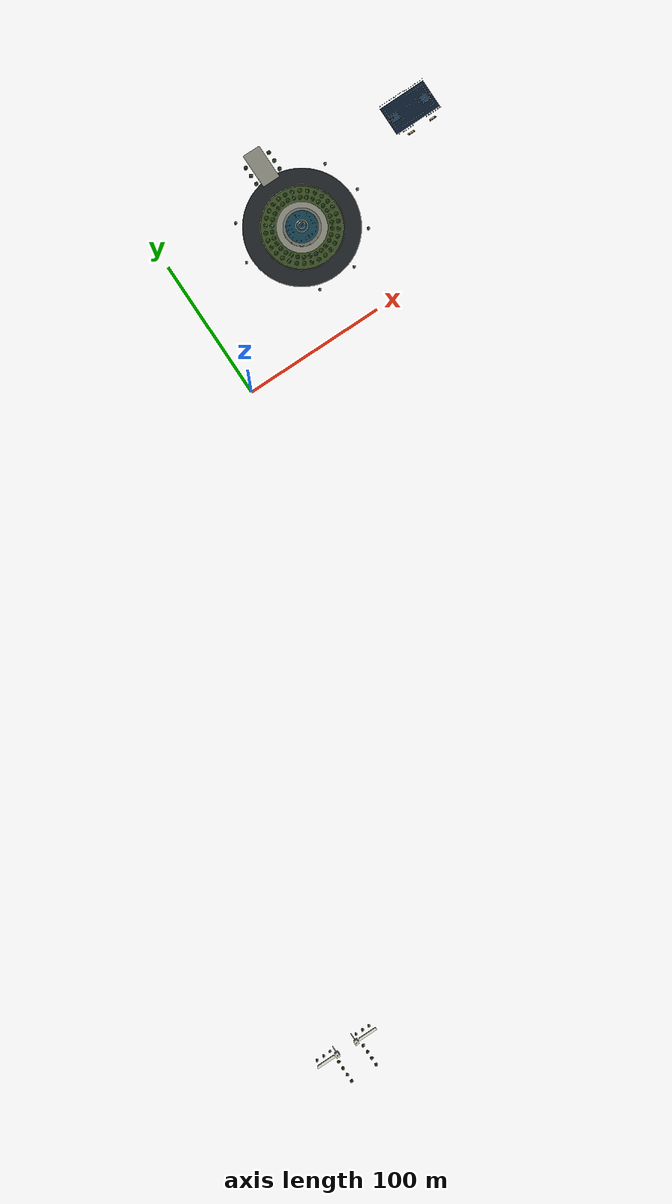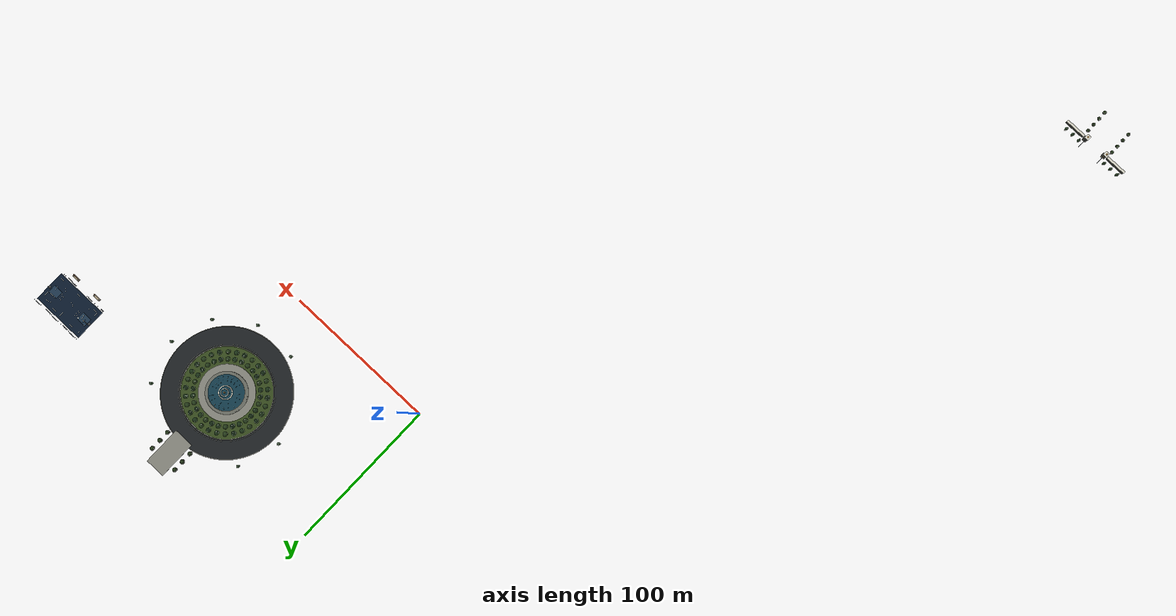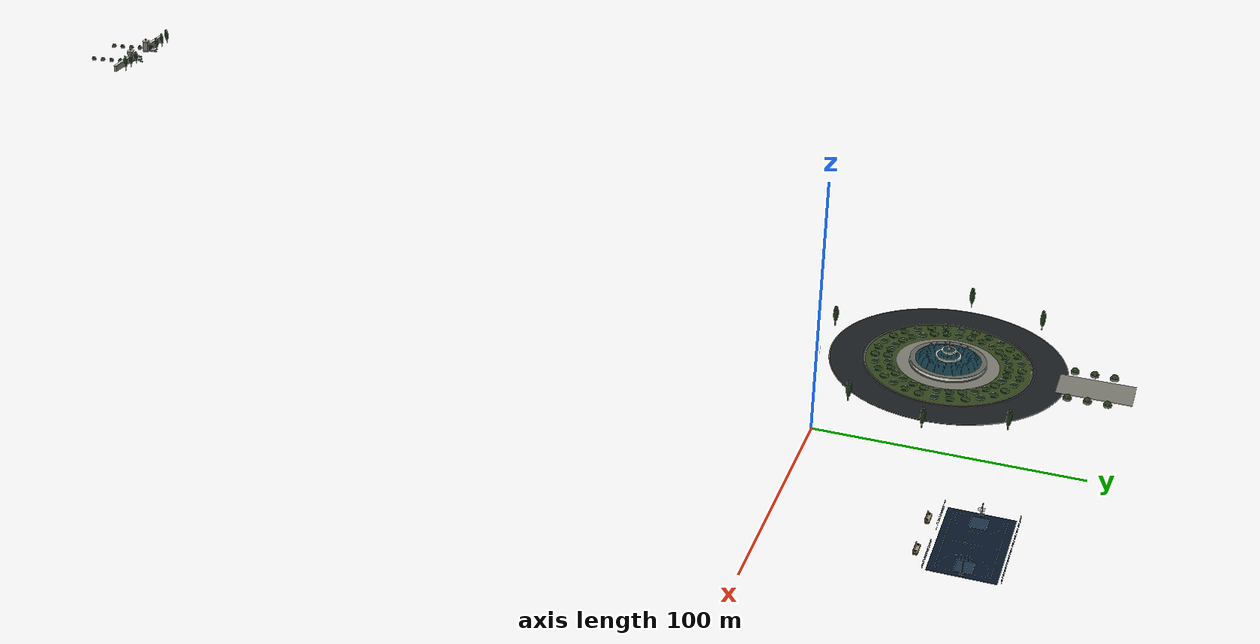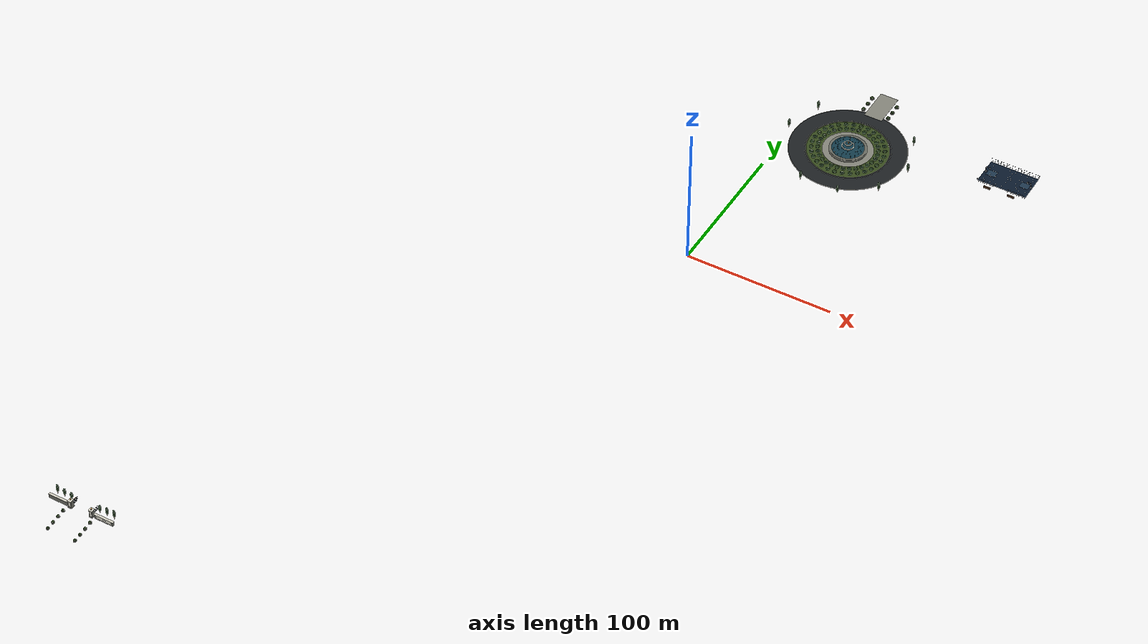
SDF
<sdf version="1.9">
 <world name="summit_estate">
  <physics name="default" type="ignored">
   <max_step_size>0.004</max_step_size>
   <real_time_factor>1.0</real_time_factor>
  </physics>
  <gravity>0 0 -9.81</gravity>
  <magnetic_field>2.15e-5 0 4.27e-5</magnetic_field>
  <plugin filename="gz-sim-physics-system" name="gz::sim::systems::Physics"/>
  <plugin filename="gz-sim-user-commands-system" name="gz::sim::systems::UserCommands"/>
  <plugin filename="gz-sim-scene-broadcaster-system" name="gz::sim::systems::SceneBroadcaster"/>
  <plugin filename="gz-sim-sensors-system" name="gz::sim::systems::Sensors">
   <render_engine>ogre2</render_engine>
  </plugin>
  <scene><ambient>.56 .58 .61 1</ambient><background>.59 .70 .78 1</background><shadows>true</shadows></scene>
  <light type="directional" name="late_afternoon_sun">
   <pose>0 0 400 0 0 0</pose>
   <diffuse>1 .88 .70 1</diffuse>
   <specular>.35 .32 .26 1</specular>
   <direction>-.35 .45 -.83</direction>
   <attenuation><range>2000</range><constant>1</constant><linear>0</linear><quadratic>0</quadratic></attenuation>
  </light>
  <include><uri>model://estate_entrance</uri></include>
  <include><uri>model://estate_arrival</uri></include>
  <include><uri>model://estate_basketball</uri></include>
  <include><uri>model://estate_lake_pavilion</uri></include>
  <include><uri>model://summit_forest_1_0</uri></include>
  <include><uri>model://summit_forest_0_0</uri></include>
  <include><uri>model://summit_forest_1_1</uri></include>
  <include><uri>model://summit_forest_0_1</uri></include>
  <include><uri>model://summit_forest_0_2</uri></include>
  <include><uri>model://summit_forest_0_3</uri></include>
  <include><uri>model://summit_forest_1_3</uri></include>
  <include><uri>model://summit_forest_1_2</uri></include>
  <frame name="uav_lawn_spawn"><pose>125 8 80.5 0 0 0</pose></frame>
 </world>
</sdf>

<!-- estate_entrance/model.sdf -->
<sdf version="1.9">
  <model name="estate_entrance">
    <static>true</static>
    <link name="structure">
      <visual name="visual_stone">
        <geometry>
          <mesh>
            <uri>model://estate_entrance/meshes/visual/stone.dae</uri>
          </mesh>
        </geometry>
        <material>
          <ambient>0.42 0.43 0.39 1</ambient>
          <diffuse>0.42 0.43 0.39 1</diffuse>
          <specular>0.15 0.15 0.15 1</specular>
          <pbr>
            <metal>
              <roughness>0.8</roughness>
              <metalness>0.0</metalness>
            </metal>
          </pbr>
        </material>
      </visual>
      <visual name="visual_paving">
        <geometry>
          <mesh>
            <uri>model://estate_entrance/meshes/visual/paving.dae</uri>
          </mesh>
        </geometry>
        <material>
          <ambient>0.53 0.53 0.49 1</ambient>
          <diffuse>0.53 0.53 0.49 1</diffuse>
          <specular>0.15 0.15 0.15 1</specular>
          <pbr>
            <metal>
              <roughness>0.8</roughness>
              <metalness>0.0</metalness>
            </metal>
          </pbr>
        </material>
      </visual>
      <visual name="visual_ivory">
        <geometry>
          <mesh>
            <uri>model://estate_entrance/meshes/visual/ivory.dae</uri>
          </mesh>
        </geometry>
        <material>
          <ambient>0.88 0.87 0.81 1</ambient>
          <diffuse>0.88 0.87 0.81 1</diffuse>
          <specular>0.15 0.15 0.15 1</specular>
          <pbr>
            <metal>
              <roughness>0.8</roughness>
              <metalness>0.0</metalness>
            </metal>
          </pbr>
        </material>
      </visual>
      <visual name="visual_metal">
        <geometry>
          <mesh>
            <uri>model://estate_entrance/meshes/visual/metal.dae</uri>
          </mesh>
        </geometry>
        <material>
          <ambient>0.21 0.23 0.24 1</ambient>
          <diffuse>0.21 0.23 0.24 1</diffuse>
          <specular>0.15 0.15 0.15 1</specular>
          <pbr>
            <metal>
              <roughness>0.35</roughness>
              <metalness>0.65</metalness>
            </metal>
          </pbr>
        </material>
      </visual>
      <visual name="visual_trunk">
        <geometry>
          <mesh>
            <uri>model://estate_entrance/meshes/visual/trunk.dae</uri>
          </mesh>
        </geometry>
        <material>
          <ambient>0.19 0.12 0.072 1</ambient>
          <diffuse>0.19 0.12 0.072 1</diffuse>
          <specular>0.15 0.15 0.15 1</specular>
          <pbr>
            <metal>
              <roughness>0.8</roughness>
              <metalness>0.0</metalness>
            </metal>
          </pbr>
        </material>
      </visual>
      <visual name="visual_charcoal">
        <geometry>
          <mesh>
            <uri>model://estate_entrance/meshes/visual/charcoal.dae</uri>
          </mesh>
        </geometry>
        <material>
          <ambient>0.045 0.054 0.06 1</ambient>
          <diffuse>0.045 0.054 0.06 1</diffuse>
          <specular>0.15 0.15 0.15 1</specular>
          <pbr>
            <metal>
              <roughness>0.8</roughness>
              <metalness>0.0</metalness>
            </metal>
          </pbr>
        </material>
      </visual>
      <visual name="visual_brass">
        <geometry>
          <mesh>
            <uri>model://estate_entrance/meshes/visual/brass.dae</uri>
          </mesh>
        </geometry>
        <material>
          <ambient>0.68 0.48 0.22 1</ambient>
          <diffuse>0.68 0.48 0.22 1</diffuse>
          <specular>0.15 0.15 0.15 1</specular>
          <pbr>
            <metal>
              <roughness>0.35</roughness>
              <metalness>0.65</metalness>
            </metal>
          </pbr>
        </material>
      </visual>
      <visual name="visual_emissive">
        <geometry>
          <mesh>
            <uri>model://estate_entrance/meshes/visual/emissive.dae</uri>
          </mesh>
        </geometry>
        <material>
          <ambient>0.94 0.73 0.36 1</ambient>
          <diffuse>0.94 0.73 0.36 1</diffuse>
          <specular>0.15 0.15 0.15 1</specular>
          <emissive>0.517 0.4015 0.198 1</emissive>
          <pbr>
            <metal>
              <roughness>0.8</roughness>
              <metalness>0.0</metalness>
            </metal>
          </pbr>
        </material>
      </visual>
      <visual name="visual_grass_dark">
        <geometry>
          <mesh>
            <uri>model://estate_entrance/meshes/visual/grass_dark.dae</uri>
          </mesh>
        </geometry>
        <material>
          <ambient>0.14 0.22 0.085 1</ambient>
          <diffuse>0.14 0.22 0.085 1</diffuse>
          <specular>0.15 0.15 0.15 1</specular>
          <pbr>
            <metal>
              <roughness>0.8</roughness>
              <metalness>0.0</metalness>
            </metal>
          </pbr>
        </material>
      </visual>
      <visual name="visual_leaf0">
        <geometry>
          <mesh>
            <uri>model://estate_entrance/meshes/visual/leaf0.dae</uri>
          </mesh>
        </geometry>
        <material>
          <ambient>0.072 0.145 0.065 1</ambient>
          <diffuse>0.072 0.145 0.065 1</diffuse>
          <specular>0.15 0.15 0.15 1</specular>
          <pbr>
            <metal>
              <roughness>0.8</roughness>
              <metalness>0.0</metalness>
            </metal>
          </pbr>
        </material>
      </visual>
      <visual name="visual_leaf1">
        <geometry>
          <mesh>
            <uri>model://estate_entrance/meshes/visual/leaf1.dae</uri>
          </mesh>
        </geometry>
        <material>
          <ambient>0.105 0.195 0.085 1</ambient>
          <diffuse>0.105 0.195 0.085 1</diffuse>
          <specular>0.15 0.15 0.15 1</specular>
          <pbr>
            <metal>
              <roughness>0.8</roughness>
              <metalness>0.0</metalness>
            </metal>
          </pbr>
        </material>
      </visual>
      <visual name="visual_leaf2">
        <geometry>
          <mesh>
            <uri>model://estate_entrance/meshes/visual/leaf2.dae</uri>
          </mesh>
        </geometry>
        <material>
          <ambient>0.15 0.235 0.105 1</ambient>
          <diffuse>0.15 0.235 0.105 1</diffuse>
          <specular>0.15 0.15 0.15 1</specular>
          <pbr>
            <metal>
              <roughness>0.8</roughness>
              <metalness>0.0</metalness>
            </metal>
          </pbr>
        </material>
      </visual>
      <visual name="visual_white">
        <geometry>
          <mesh>
            <uri>model://estate_entrance/meshes/visual/white.dae</uri>
          </mesh>
        </geometry>
        <material>
          <ambient>0.93 0.93 0.89 1</ambient>
          <diffuse>0.93 0.93 0.89 1</diffuse>
          <specular>0.15 0.15 0.15 1</specular>
          <pbr>
            <metal>
              <roughness>0.8</roughness>
              <metalness>0.0</metalness>
            </metal>
          </pbr>
        </material>
      </visual>
      <collision name="west_gate_pier">
        <geometry>
          <box>
            <size>2.2 2.5 5.4</size>
          </box>
        </geometry>
        <pose>-192.4 -390 29.1 0 0 0</pose>
      </collision>
      <collision name="west_pier_base">
        <geometry>
          <box>
            <size>2.7 2.9 0.5</size>
          </box>
        </geometry>
        <pose>-192.4 -390 26.65 0 0 0</pose>
      </collision>
      <collision name="west_pier_cap">
        <geometry>
          <box>
            <size>2.65 2.95 0.3</size>
          </box>
        </geometry>
        <pose>-192.4 -390 31.83 0 0 0</pose>
      </collision>
      <collision name="west_leaf_rail_0.5">
        <geometry>
          <box>
            <size>0.14 5.9 0.12</size>
          </box>
        </geometry>
        <pose>-192.2 -386.8 26.9 0 0 0</pose>
      </collision>
      <collision name="west_leaf_rail_1.25">
        <geometry>
          <box>
            <size>0.14 5.9 0.12</size>
          </box>
        </geometry>
        <pose>-192.2 -386.8 27.65 0 0 0</pose>
      </collision>
      <collision name="west_leaf_rail_2.9">
        <geometry>
          <box>
            <size>0.14 5.9 0.12</size>
          </box>
        </geometry>
        <pose>-192.2 -386.8 29.3 0 0 0</pose>
      </collision>
      <collision name="west_picket_0">
        <geometry>
          <box>
            <size>0.065 0.065 2.95</size>
          </box>
        </geometry>
        <pose>-192.2 -389.7 28.025 0 0 0</pose>
      </collision>
      <collision name="west_picket_1">
        <geometry>
          <box>
            <size>0.065 0.065 3.01257</size>
          </box>
        </geometry>
        <pose>-192.2 -389.41 28.0563 0 0 0</pose>
      </collision>
      <collision name="west_picket_2">
        <geometry>
          <box>
            <size>0.065 0.065 3.07361</size>
          </box>
        </geometry>
        <pose>-192.2 -389.12 28.0868 0 0 0</pose>
      </collision>
      <collision name="west_picket_3">
        <geometry>
          <box>
            <size>0.065 0.065 3.1316</size>
          </box>
        </geometry>
        <pose>-192.2 -388.83 28.1158 0 0 0</pose>
      </collision>
      <collision name="west_picket_4">
        <geometry>
          <box>
            <size>0.065 0.065 3.18511</size>
          </box>
        </geometry>
        <pose>-192.2 -388.54 28.1426 0 0 0</pose>
      </collision>
      <collision name="west_picket_5">
        <geometry>
          <box>
            <size>0.065 0.065 3.23284</size>
          </box>
        </geometry>
        <pose>-192.2 -388.25 28.1664 0 0 0</pose>
      </collision>
      <collision name="west_picket_6">
        <geometry>
          <box>
            <size>0.065 0.065 3.27361</size>
          </box>
        </geometry>
        <pose>-192.2 -387.96 28.1868 0 0 0</pose>
      </collision>
      <collision name="west_picket_7">
        <geometry>
          <box>
            <size>0.065 0.065 3.3064</size>
          </box>
        </geometry>
        <pose>-192.2 -387.67 28.2032 0 0 0</pose>
      </collision>
      <collision name="west_picket_8">
        <geometry>
          <box>
            <size>0.065 0.065 3.33042</size>
          </box>
        </geometry>
        <pose>-192.2 -387.38 28.2152 0 0 0</pose>
      </collision>
      <collision name="west_picket_9">
        <geometry>
          <box>
            <size>0.065 0.065 3.34508</size>
          </box>
        </geometry>
        <pose>-192.2 -387.09 28.2225 0 0 0</pose>
      </collision>
      <collision name="west_picket_10">
        <geometry>
          <box>
            <size>0.065 0.065 3.35</size>
          </box>
        </geometry>
        <pose>-192.2 -386.8 28.225 0 0 0</pose>
      </collision>
      <collision name="west_picket_11">
        <geometry>
          <box>
            <size>0.065 0.065 3.34508</size>
          </box>
        </geometry>
        <pose>-192.2 -386.51 28.2225 0 0 0</pose>
      </collision>
      <collision name="west_picket_12">
        <geometry>
          <box>
            <size>0.065 0.065 3.33042</size>
          </box>
        </geometry>
        <pose>-192.2 -386.22 28.2152 0 0 0</pose>
      </collision>
      <collision name="west_picket_13">
        <geometry>
          <box>
            <size>0.065 0.065 3.3064</size>
          </box>
        </geometry>
        <pose>-192.2 -385.93 28.2032 0 0 0</pose>
      </collision>
      <collision name="west_picket_14">
        <geometry>
          <box>
            <size>0.065 0.065 3.27361</size>
          </box>
        </geometry>
        <pose>-192.2 -385.64 28.1868 0 0 0</pose>
      </collision>
      <collision name="west_picket_15">
        <geometry>
          <box>
            <size>0.065 0.065 3.23284</size>
          </box>
        </geometry>
        <pose>-192.2 -385.35 28.1664 0 0 0</pose>
      </collision>
      <collision name="west_picket_16">
        <geometry>
          <box>
            <size>0.065 0.065 3.18511</size>
          </box>
        </geometry>
        <pose>-192.2 -385.06 28.1426 0 0 0</pose>
      </collision>
      <collision name="west_picket_17">
        <geometry>
          <box>
            <size>0.065 0.065 3.1316</size>
          </box>
        </geometry>
        <pose>-192.2 -384.77 28.1158 0 0 0</pose>
      </collision>
      <collision name="west_picket_18">
        <geometry>
          <box>
            <size>0.065 0.065 3.07361</size>
          </box>
        </geometry>
        <pose>-192.2 -384.48 28.0868 0 0 0</pose>
      </collision>
      <collision name="west_picket_19">
        <geometry>
          <box>
            <size>0.065 0.065 3.01257</size>
          </box>
        </geometry>
        <pose>-192.2 -384.19 28.0563 0 0 0</pose>
      </collision>
      <collision name="west_picket_20">
        <geometry>
          <box>
            <size>0.065 0.065 2.95</size>
          </box>
        </geometry>
        <pose>-192.2 -383.9 28.025 0 0 0</pose>
      </collision>
      <collision name="west_entry_wing">
        <geometry>
          <box>
            <size>13 1.3 3</size>
          </box>
        </geometry>
        <pose>-201 -390 27.9 0 0 0</pose>
      </collision>
      <collision name="west_wing_cap">
        <geometry>
          <box>
            <size>13.4 1.5 0.22</size>
          </box>
        </geometry>
        <pose>-201 -390 29.45 0 0 0</pose>
      </collision>
      <collision name="west_entry_cypress_0_trunk">
        <geometry>
          <cylinder>
            <radius>0.2</radius>
            <length>3.1</length>
          </cylinder>
        </geometry>
        <pose>-195 -385.5 28.3 0 0 0</pose>
      </collision>
      <collision name="west_entry_cypress_1_trunk">
        <geometry>
          <cylinder>
            <radius>0.2</radius>
            <length>3.4</length>
          </cylinder>
        </geometry>
        <pose>-200 -385.5 28.45 0 0 0</pose>
      </collision>
      <collision name="west_entry_cypress_2_trunk">
        <geometry>
          <cylinder>
            <radius>0.2</radius>
            <length>3.7</length>
          </cylinder>
        </geometry>
        <pose>-205 -385.5 28.6 0 0 0</pose>
      </collision>
      <collision name="west_approach_planter_0">
        <geometry>
          <cylinder>
            <radius>1.05</radius>
            <length>0.72</length>
          </cylinder>
        </geometry>
        <pose>-194.5 -395 26.46 0 0 0</pose>
      </collision>
      <collision name="west_approach_planter_1">
        <geometry>
          <cylinder>
            <radius>1.05</radius>
            <length>0.72</length>
          </cylinder>
        </geometry>
        <pose>-194.5 -400 26.14 0 0 0</pose>
      </collision>
      <collision name="west_approach_planter_2">
        <geometry>
          <cylinder>
            <radius>1.05</radius>
            <length>0.72</length>
          </cylinder>
        </geometry>
        <pose>-194.5 -405 25.82 0 0 0</pose>
      </collision>
      <collision name="west_approach_planter_3">
        <geometry>
          <cylinder>
            <radius>1.05</radius>
            <length>0.72</length>
          </cylinder>
        </geometry>
        <pose>-194.5 -410 25.5 0 0 0</pose>
      </collision>
      <collision name="east_gate_pier">
        <geometry>
          <box>
            <size>2.2 2.5 5.4</size>
          </box>
        </geometry>
        <pose>-177.6 -390 29.1 0 0 0</pose>
      </collision>
      <collision name="east_pier_base">
        <geometry>
          <box>
            <size>2.7 2.9 0.5</size>
          </box>
        </geometry>
        <pose>-177.6 -390 26.65 0 0 0</pose>
      </collision>
      <collision name="east_pier_cap">
        <geometry>
          <box>
            <size>2.65 2.95 0.3</size>
          </box>
        </geometry>
        <pose>-177.6 -390 31.83 0 0 0</pose>
      </collision>
      <collision name="east_leaf_rail_0.5">
        <geometry>
          <box>
            <size>0.14 5.9 0.12</size>
          </box>
        </geometry>
        <pose>-177.8 -386.8 26.9 0 0 0</pose>
      </collision>
      <collision name="east_leaf_rail_1.25">
        <geometry>
          <box>
            <size>0.14 5.9 0.12</size>
          </box>
        </geometry>
        <pose>-177.8 -386.8 27.65 0 0 0</pose>
      </collision>
      <collision name="east_leaf_rail_2.9">
        <geometry>
          <box>
            <size>0.14 5.9 0.12</size>
          </box>
        </geometry>
        <pose>-177.8 -386.8 29.3 0 0 0</pose>
      </collision>
      <collision name="east_picket_0">
        <geometry>
          <box>
            <size>0.065 0.065 2.95</size>
          </box>
        </geometry>
        <pose>-177.8 -389.7 28.025 0 0 0</pose>
      </collision>
      <collision name="east_picket_1">
        <geometry>
          <box>
            <size>0.065 0.065 3.01257</size>
          </box>
        </geometry>
        <pose>-177.8 -389.41 28.0563 0 0 0</pose>
      </collision>
      <collision name="east_picket_2">
        <geometry>
          <box>
            <size>0.065 0.065 3.07361</size>
          </box>
        </geometry>
        <pose>-177.8 -389.12 28.0868 0 0 0</pose>
      </collision>
      <collision name="east_picket_3">
        <geometry>
          <box>
            <size>0.065 0.065 3.1316</size>
          </box>
        </geometry>
        <pose>-177.8 -388.83 28.1158 0 0 0</pose>
      </collision>
      <collision name="east_picket_4">
        <geometry>
          <box>
            <size>0.065 0.065 3.18511</size>
          </box>
        </geometry>
        <pose>-177.8 -388.54 28.1426 0 0 0</pose>
      </collision>
      <collision name="east_picket_5">
        <geometry>
          <box>
            <size>0.065 0.065 3.23284</size>
          </box>
        </geometry>
        <pose>-177.8 -388.25 28.1664 0 0 0</pose>
      </collision>
      <collision name="east_picket_6">
        <geometry>
          <box>
            <size>0.065 0.065 3.27361</size>
          </box>
        </geometry>
        <pose>-177.8 -387.96 28.1868 0 0 0</pose>
      </collision>
      <collision name="east_picket_7">
        <geometry>
          <box>
            <size>0.065 0.065 3.3064</size>
          </box>
        </geometry>
        <pose>-177.8 -387.67 28.2032 0 0 0</pose>
      </collision>
      <collision name="east_picket_8">
        <geometry>
          <box>
            <size>0.065 0.065 3.33042</size>
          </box>
        </geometry>
        <pose>-177.8 -387.38 28.2152 0 0 0</pose>
      </collision>
      <collision name="east_picket_9">
        <geometry>
          <box>
            <size>0.065 0.065 3.34508</size>
          </box>
        </geometry>
        <pose>-177.8 -387.09 28.2225 0 0 0</pose>
      </collision>
      <collision name="east_picket_10">
        <geometry>
          <box>
            <size>0.065 0.065 3.35</size>
          </box>
        </geometry>
        <pose>-177.8 -386.8 28.225 0 0 0</pose>
      </collision>
      <collision name="east_picket_11">
        <geometry>
          <box>
            <size>0.065 0.065 3.34508</size>
          </box>
        </geometry>
        <pose>-177.8 -386.51 28.2225 0 0 0</pose>
      </collision>
      <collision name="east_picket_12">
        <geometry>
          <box>
            <size>0.065 0.065 3.33042</size>
          </box>
        </geometry>
        <pose>-177.8 -386.22 28.2152 0 0 0</pose>
      </collision>
      <collision name="east_picket_13">
        <geometry>
          <box>
            <size>0.065 0.065 3.3064</size>
          </box>
        </geometry>
        <pose>-177.8 -385.93 28.2032 0 0 0</pose>
      </collision>
      <collision name="east_picket_14">
        <geometry>
          <box>
            <size>0.065 0.065 3.27361</size>
          </box>
        </geometry>
        <pose>-177.8 -385.64 28.1868 0 0 0</pose>
      </collision>
      <collision name="east_picket_15">
        <geometry>
          <box>
            <size>0.065 0.065 3.23284</size>
          </box>
        </geometry>
        <pose>-177.8 -385.35 28.1664 0 0 0</pose>
      </collision>
      <collision name="east_picket_16">
        <geometry>
          <box>
            <size>0.065 0.065 3.18511</size>
          </box>
        </geometry>
        <pose>-177.8 -385.06 28.1426 0 0 0</pose>
      </collision>
      <collision name="east_picket_17">
        <geometry>
          <box>
            <size>0.065 0.065 3.1316</size>
          </box>
        </geometry>
        <pose>-177.8 -384.77 28.1158 0 0 0</pose>
      </collision>
      <collision name="east_picket_18">
        <geometry>
          <box>
            <size>0.065 0.065 3.07361</size>
          </box>
        </geometry>
        <pose>-177.8 -384.48 28.0868 0 0 0</pose>
      </collision>
      <collision name="east_picket_19">
        <geometry>
          <box>
            <size>0.065 0.065 3.01257</size>
          </box>
        </geometry>
        <pose>-177.8 -384.19 28.0563 0 0 0</pose>
      </collision>
      <collision name="east_picket_20">
        <geometry>
          <box>
            <size>0.065 0.065 2.95</size>
          </box>
        </geometry>
        <pose>-177.8 -383.9 28.025 0 0 0</pose>
      </collision>
      <collision name="east_entry_wing">
        <geometry>
          <box>
            <size>13 1.3 3</size>
          </box>
        </geometry>
        <pose>-169 -390 27.9 0 0 0</pose>
      </collision>
      <collision name="east_wing_cap">
        <geometry>
          <box>
            <size>13.4 1.5 0.22</size>
          </box>
        </geometry>
        <pose>-169 -390 29.45 0 0 0</pose>
      </collision>
      <collision name="east_entry_cypress_0_trunk">
        <geometry>
          <cylinder>
            <radius>0.2</radius>
            <length>3.1</length>
          </cylinder>
        </geometry>
        <pose>-175 -385.5 28.3 0 0 0</pose>
      </collision>
      <collision name="east_entry_cypress_1_trunk">
        <geometry>
          <cylinder>
            <radius>0.2</radius>
            <length>3.4</length>
          </cylinder>
        </geometry>
        <pose>-170 -385.5 28.45 0 0 0</pose>
      </collision>
      <collision name="east_entry_cypress_2_trunk">
        <geometry>
          <cylinder>
            <radius>0.2</radius>
            <length>3.7</length>
          </cylinder>
        </geometry>
        <pose>-165 -385.5 28.6 0 0 0</pose>
      </collision>
      <collision name="east_approach_planter_0">
        <geometry>
          <cylinder>
            <radius>1.05</radius>
            <length>0.72</length>
          </cylinder>
        </geometry>
        <pose>-175.5 -395 26.46 0 0 0</pose>
      </collision>
      <collision name="east_approach_planter_1">
        <geometry>
          <cylinder>
            <radius>1.05</radius>
            <length>0.72</length>
          </cylinder>
        </geometry>
        <pose>-175.5 -400 26.14 0 0 0</pose>
      </collision>
      <collision name="east_approach_planter_2">
        <geometry>
          <cylinder>
            <radius>1.05</radius>
            <length>0.72</length>
          </cylinder>
        </geometry>
        <pose>-175.5 -405 25.82 0 0 0</pose>
      </collision>
      <collision name="east_approach_planter_3">
        <geometry>
          <cylinder>
            <radius>1.05</radius>
            <length>0.72</length>
          </cylinder>
        </geometry>
        <pose>-175.5 -410 25.5 0 0 0</pose>
      </collision>
    </link>
  </model>
</sdf>

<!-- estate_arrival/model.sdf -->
<sdf version="1.9">
  <model name="estate_arrival">
    <static>true</static>
    <link name="structure">
      <visual name="visual_asphalt">
        <geometry>
          <mesh>
            <uri>model://estate_arrival/meshes/visual/asphalt.dae</uri>
          </mesh>
        </geometry>
        <material>
          <ambient>0.12 0.135 0.145 1</ambient>
          <diffuse>0.12 0.135 0.145 1</diffuse>
          <specular>0.15 0.15 0.15 1</specular>
          <pbr>
            <metal>
              <roughness>0.8</roughness>
              <metalness>0.0</metalness>
            </metal>
          </pbr>
        </material>
      </visual>
      <visual name="visual_stone">
        <geometry>
          <mesh>
            <uri>model://estate_arrival/meshes/visual/stone.dae</uri>
          </mesh>
        </geometry>
        <material>
          <ambient>0.42 0.43 0.39 1</ambient>
          <diffuse>0.42 0.43 0.39 1</diffuse>
          <specular>0.15 0.15 0.15 1</specular>
          <pbr>
            <metal>
              <roughness>0.8</roughness>
              <metalness>0.0</metalness>
            </metal>
          </pbr>
        </material>
      </visual>
      <visual name="visual_paving">
        <geometry>
          <mesh>
            <uri>model://estate_arrival/meshes/visual/paving.dae</uri>
          </mesh>
        </geometry>
        <material>
          <ambient>0.53 0.53 0.49 1</ambient>
          <diffuse>0.53 0.53 0.49 1</diffuse>
          <specular>0.15 0.15 0.15 1</specular>
          <pbr>
            <metal>
              <roughness>0.8</roughness>
              <metalness>0.0</metalness>
            </metal>
          </pbr>
        </material>
      </visual>
      <visual name="visual_ivory">
        <geometry>
          <mesh>
            <uri>model://estate_arrival/meshes/visual/ivory.dae</uri>
          </mesh>
        </geometry>
        <material>
          <ambient>0.88 0.87 0.81 1</ambient>
          <diffuse>0.88 0.87 0.81 1</diffuse>
          <specular>0.15 0.15 0.15 1</specular>
          <pbr>
            <metal>
              <roughness>0.8</roughness>
              <metalness>0.0</metalness>
            </metal>
          </pbr>
        </material>
      </visual>
      <visual name="visual_trunk">
        <geometry>
          <mesh>
            <uri>model://estate_arrival/meshes/visual/trunk.dae</uri>
          </mesh>
        </geometry>
        <material>
          <ambient>0.19 0.12 0.072 1</ambient>
          <diffuse>0.19 0.12 0.072 1</diffuse>
          <specular>0.15 0.15 0.15 1</specular>
          <pbr>
            <metal>
              <roughness>0.8</roughness>
              <metalness>0.0</metalness>
            </metal>
          </pbr>
        </material>
      </visual>
      <visual name="visual_brass">
        <geometry>
          <mesh>
            <uri>model://estate_arrival/meshes/visual/brass.dae</uri>
          </mesh>
        </geometry>
        <material>
          <ambient>0.68 0.48 0.22 1</ambient>
          <diffuse>0.68 0.48 0.22 1</diffuse>
          <specular>0.15 0.15 0.15 1</specular>
          <pbr>
            <metal>
              <roughness>0.35</roughness>
              <metalness>0.65</metalness>
            </metal>
          </pbr>
        </material>
      </visual>
      <visual name="visual_grass">
        <geometry>
          <mesh>
            <uri>model://estate_arrival/meshes/visual/grass.dae</uri>
          </mesh>
        </geometry>
        <material>
          <ambient>0.22 0.3 0.12 1</ambient>
          <diffuse>0.22 0.3 0.12 1</diffuse>
          <specular>0.15 0.15 0.15 1</specular>
          <pbr>
            <metal>
              <roughness>0.8</roughness>
              <metalness>0.0</metalness>
            </metal>
          </pbr>
        </material>
      </visual>
      <visual name="visual_grass_dark">
        <geometry>
          <mesh>
            <uri>model://estate_arrival/meshes/visual/grass_dark.dae</uri>
          </mesh>
        </geometry>
        <material>
          <ambient>0.14 0.22 0.085 1</ambient>
          <diffuse>0.14 0.22 0.085 1</diffuse>
          <specular>0.15 0.15 0.15 1</specular>
          <pbr>
            <metal>
              <roughness>0.8</roughness>
              <metalness>0.0</metalness>
            </metal>
          </pbr>
        </material>
      </visual>
      <visual name="visual_leaf0">
        <geometry>
          <mesh>
            <uri>model://estate_arrival/meshes/visual/leaf0.dae</uri>
          </mesh>
        </geometry>
        <material>
          <ambient>0.072 0.145 0.065 1</ambient>
          <diffuse>0.072 0.145 0.065 1</diffuse>
          <specular>0.15 0.15 0.15 1</specular>
          <pbr>
            <metal>
              <roughness>0.8</roughness>
              <metalness>0.0</metalness>
            </metal>
          </pbr>
        </material>
      </visual>
      <visual name="visual_leaf1">
        <geometry>
          <mesh>
            <uri>model://estate_arrival/meshes/visual/leaf1.dae</uri>
          </mesh>
        </geometry>
        <material>
          <ambient>0.105 0.195 0.085 1</ambient>
          <diffuse>0.105 0.195 0.085 1</diffuse>
          <specular>0.15 0.15 0.15 1</specular>
          <pbr>
            <metal>
              <roughness>0.8</roughness>
              <metalness>0.0</metalness>
            </metal>
          </pbr>
        </material>
      </visual>
      <visual name="visual_leaf2">
        <geometry>
          <mesh>
            <uri>model://estate_arrival/meshes/visual/leaf2.dae</uri>
          </mesh>
        </geometry>
        <material>
          <ambient>0.15 0.235 0.105 1</ambient>
          <diffuse>0.15 0.235 0.105 1</diffuse>
          <specular>0.15 0.15 0.15 1</specular>
          <pbr>
            <metal>
              <roughness>0.8</roughness>
              <metalness>0.0</metalness>
            </metal>
          </pbr>
        </material>
      </visual>
      <visual name="visual_water">
        <geometry>
          <mesh>
            <uri>model://estate_arrival/meshes/visual/water.dae</uri>
          </mesh>
        </geometry>
        <material>
          <ambient>0.075 0.24 0.3 1</ambient>
          <diffuse>0.075 0.24 0.3 1</diffuse>
          <specular>0.15 0.15 0.15 1</specular>
          <pbr>
            <metal>
              <roughness>0.16</roughness>
              <metalness>0.0</metalness>
            </metal>
          </pbr>
        </material>
      </visual>
      <visual name="visual_white">
        <geometry>
          <mesh>
            <uri>model://estate_arrival/meshes/visual/white.dae</uri>
          </mesh>
        </geometry>
        <material>
          <ambient>0.93 0.93 0.89 1</ambient>
          <diffuse>0.93 0.93 0.89 1</diffuse>
          <specular>0.15 0.15 0.15 1</specular>
          <pbr>
            <metal>
              <roughness>0.8</roughness>
              <metalness>0.0</metalness>
            </metal>
          </pbr>
        </material>
      </visual>
      <collision name="arrival_drive">
        <geometry>
          <mesh>
            <uri>model://estate_arrival/meshes/collision/arrival_drive.dae</uri>
          </mesh>
        </geometry>
      </collision>
      <collision name="inner_drive_curb">
        <geometry>
          <mesh>
            <uri>model://estate_arrival/meshes/collision/inner_drive_curb.dae</uri>
          </mesh>
        </geometry>
      </collision>
      <collision name="fountain_walk">
        <geometry>
          <mesh>
            <uri>model://estate_arrival/meshes/collision/fountain_walk.dae</uri>
          </mesh>
        </geometry>
      </collision>
      <collision name="fountain_base">
        <geometry>
          <cylinder>
            <radius>12</radius>
            <length>0.48</length>
          </cylinder>
        </geometry>
        <pose>78 58 80.24 0 0 0</pose>
      </collision>
      <collision name="fountain_basin">
        <geometry>
          <mesh>
            <uri>model://estate_arrival/meshes/collision/fountain_basin.dae</uri>
          </mesh>
        </geometry>
      </collision>
      <collision name="fountain_coping">
        <geometry>
          <mesh>
            <uri>model://estate_arrival/meshes/collision/fountain_coping.dae</uri>
          </mesh>
        </geometry>
      </collision>
      <collision name="fountain_pedestal">
        <geometry>
          <cylinder>
            <radius>1.05</radius>
            <length>3.2</length>
          </cylinder>
        </geometry>
        <pose>78 58 81.85 0 0 0</pose>
      </collision>
      <collision name="fountain_middle_bowl">
        <geometry>
          <mesh>
            <uri>model://estate_arrival/meshes/collision/fountain_middle_bowl.dae</uri>
          </mesh>
        </geometry>
      </collision>
      <collision name="fountain_middle_floor">
        <geometry>
          <cylinder>
            <radius>3.95</radius>
            <length>0.18</length>
          </cylinder>
        </geometry>
        <pose>78 58 82.89 0 0 0</pose>
      </collision>
      <collision name="fountain_upper_stem">
        <geometry>
          <cylinder>
            <radius>0.56</radius>
            <length>2.0</length>
          </cylinder>
        </geometry>
        <pose>78 58 83.95 0 0 0</pose>
      </collision>
      <collision name="fountain_upper_bowl">
        <geometry>
          <mesh>
            <uri>model://estate_arrival/meshes/collision/fountain_upper_bowl.dae</uri>
          </mesh>
        </geometry>
      </collision>
      <collision name="fountain_upper_floor">
        <geometry>
          <cylinder>
            <radius>2.3</radius>
            <length>0.18</length>
          </cylinder>
        </geometry>
        <pose>78 58 84.78 0 0 0</pose>
      </collision>
      <collision name="arrival_cypress_0_trunk">
        <geometry>
          <cylinder>
            <radius>0.2</radius>
            <length>3.5</length>
          </cylinder>
        </geometry>
        <pose>119 58 81.75 0 0 0</pose>
      </collision>
      <collision name="arrival_cypress_1_trunk">
        <geometry>
          <cylinder>
            <radius>0.2</radius>
            <length>3.5</length>
          </cylinder>
        </geometry>
        <pose>111.17 82.0992 81.75 0 0 0</pose>
      </collision>
      <collision name="arrival_cypress_4_trunk">
        <geometry>
          <cylinder>
            <radius>0.2</radius>
            <length>3.5</length>
          </cylinder>
        </geometry>
        <pose>44.8303 82.0992 81.75 0 0 0</pose>
      </collision>
      <collision name="arrival_cypress_5_trunk">
        <geometry>
          <cylinder>
            <radius>0.2</radius>
            <length>3.5</length>
          </cylinder>
        </geometry>
        <pose>37 58 81.75 0 0 0</pose>
      </collision>
      <collision name="arrival_cypress_7_trunk">
        <geometry>
          <cylinder>
            <radius>0.2</radius>
            <length>3.5</length>
          </cylinder>
        </geometry>
        <pose>65.3303 19.0067 81.75 0 0 0</pose>
      </collision>
      <collision name="arrival_cypress_8_trunk">
        <geometry>
          <cylinder>
            <radius>0.2</radius>
            <length>3.5</length>
          </cylinder>
        </geometry>
        <pose>90.6697 19.0067 81.75 0 0 0</pose>
      </collision>
      <collision name="arrival_cypress_9_trunk">
        <geometry>
          <cylinder>
            <radius>0.2</radius>
            <length>3.5</length>
          </cylinder>
        </geometry>
        <pose>111.17 33.9008 81.75 0 0 0</pose>
      </collision>
      <collision name="villa_entry_walk">
        <geometry>
          <box>
            <size>12 23 0.2</size>
          </box>
        </geometry>
        <pose>78 103.5 80.1 0 0 0</pose>
      </collision>
      <collision name="entry_walk_planter_-1_0">
        <geometry>
          <cylinder>
            <radius>1.3</radius>
            <length>0.72</length>
          </cylinder>
        </geometry>
        <pose>69.4 96 80.36 0 0 0</pose>
      </collision>
      <collision name="entry_walk_planter_-1_1">
        <geometry>
          <cylinder>
            <radius>1.3</radius>
            <length>0.72</length>
          </cylinder>
        </geometry>
        <pose>69.4 102 80.36 0 0 0</pose>
      </collision>
      <collision name="entry_walk_planter_-1_2">
        <geometry>
          <cylinder>
            <radius>1.3</radius>
            <length>0.72</length>
          </cylinder>
        </geometry>
        <pose>69.4 108 80.36 0 0 0</pose>
      </collision>
      <collision name="entry_walk_planter_1_0">
        <geometry>
          <cylinder>
            <radius>1.3</radius>
            <length>0.72</length>
          </cylinder>
        </geometry>
        <pose>86.6 96 80.36 0 0 0</pose>
      </collision>
      <collision name="entry_walk_planter_1_1">
        <geometry>
          <cylinder>
            <radius>1.3</radius>
            <length>0.72</length>
          </cylinder>
        </geometry>
        <pose>86.6 102 80.36 0 0 0</pose>
      </collision>
      <collision name="entry_walk_planter_1_2">
        <geometry>
          <cylinder>
            <radius>1.3</radius>
            <length>0.72</length>
          </cylinder>
        </geometry>
        <pose>86.6 108 80.36 0 0 0</pose>
      </collision>
    </link>
  </model>
</sdf>

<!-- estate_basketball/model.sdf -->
<sdf version="1.9">
  <model name="estate_basketball">
    <static>true</static>
    <link name="structure">
      <visual name="visual_court">
        <geometry>
          <mesh>
            <uri>model://estate_basketball/meshes/visual/court.dae</uri>
          </mesh>
        </geometry>
        <material>
          <ambient>0.045 0.105 0.18 1</ambient>
          <diffuse>0.045 0.105 0.18 1</diffuse>
          <specular>0.15 0.15 0.15 1</specular>
          <pbr>
            <metal>
              <roughness>0.8</roughness>
              <metalness>0.0</metalness>
            </metal>
          </pbr>
        </material>
      </visual>
      <visual name="visual_rubber">
        <geometry>
          <mesh>
            <uri>model://estate_basketball/meshes/visual/rubber.dae</uri>
          </mesh>
        </geometry>
        <material>
          <ambient>0.035 0.042 0.045 1</ambient>
          <diffuse>0.035 0.042 0.045 1</diffuse>
          <specular>0.15 0.15 0.15 1</specular>
          <pbr>
            <metal>
              <roughness>0.8</roughness>
              <metalness>0.0</metalness>
            </metal>
          </pbr>
        </material>
      </visual>
      <visual name="visual_metal">
        <geometry>
          <mesh>
            <uri>model://estate_basketball/meshes/visual/metal.dae</uri>
          </mesh>
        </geometry>
        <material>
          <ambient>0.21 0.23 0.24 1</ambient>
          <diffuse>0.21 0.23 0.24 1</diffuse>
          <specular>0.15 0.15 0.15 1</specular>
          <pbr>
            <metal>
              <roughness>0.35</roughness>
              <metalness>0.65</metalness>
            </metal>
          </pbr>
        </material>
      </visual>
      <visual name="visual_glass">
        <geometry>
          <mesh>
            <uri>model://estate_basketball/meshes/visual/glass.dae</uri>
          </mesh>
        </geometry>
        <material>
          <ambient>0.36 0.58 0.63 1</ambient>
          <diffuse>0.36 0.58 0.63 1</diffuse>
          <specular>0.15 0.15 0.15 1</specular>
          <pbr>
            <metal>
              <roughness>0.16</roughness>
              <metalness>0.0</metalness>
            </metal>
          </pbr>
        </material>
        <transparency>0.78</transparency>
        <cast_shadows>false</cast_shadows>
      </visual>
      <visual name="visual_brass">
        <geometry>
          <mesh>
            <uri>model://estate_basketball/meshes/visual/brass.dae</uri>
          </mesh>
        </geometry>
        <material>
          <ambient>0.68 0.48 0.22 1</ambient>
          <diffuse>0.68 0.48 0.22 1</diffuse>
          <specular>0.15 0.15 0.15 1</specular>
          <pbr>
            <metal>
              <roughness>0.35</roughness>
              <metalness>0.65</metalness>
            </metal>
          </pbr>
        </material>
      </visual>
      <visual name="visual_wood">
        <geometry>
          <mesh>
            <uri>model://estate_basketball/meshes/visual/wood.dae</uri>
          </mesh>
        </geometry>
        <material>
          <ambient>0.3 0.18 0.095 1</ambient>
          <diffuse>0.3 0.18 0.095 1</diffuse>
          <specular>0.15 0.15 0.15 1</specular>
          <pbr>
            <metal>
              <roughness>0.8</roughness>
              <metalness>0.0</metalness>
            </metal>
          </pbr>
        </material>
      </visual>
      <visual name="visual_court_key">
        <geometry>
          <mesh>
            <uri>model://estate_basketball/meshes/visual/court_key.dae</uri>
          </mesh>
        </geometry>
        <material>
          <ambient>0.12 0.22 0.31 1</ambient>
          <diffuse>0.12 0.22 0.31 1</diffuse>
          <specular>0.15 0.15 0.15 1</specular>
          <pbr>
            <metal>
              <roughness>0.8</roughness>
              <metalness>0.0</metalness>
            </metal>
          </pbr>
        </material>
      </visual>
      <visual name="visual_dark_fabric">
        <geometry>
          <mesh>
            <uri>model://estate_basketball/meshes/visual/dark_fabric.dae</uri>
          </mesh>
        </geometry>
        <material>
          <ambient>0.095 0.12 0.14 1</ambient>
          <diffuse>0.095 0.12 0.14 1</diffuse>
          <specular>0.15 0.15 0.15 1</specular>
          <pbr>
            <metal>
              <roughness>0.8</roughness>
              <metalness>0.0</metalness>
            </metal>
          </pbr>
        </material>
      </visual>
      <visual name="visual_fabric">
        <geometry>
          <mesh>
            <uri>model://estate_basketball/meshes/visual/fabric.dae</uri>
          </mesh>
        </geometry>
        <material>
          <ambient>0.7 0.64 0.52 1</ambient>
          <diffuse>0.7 0.64 0.52 1</diffuse>
          <specular>0.15 0.15 0.15 1</specular>
          <pbr>
            <metal>
              <roughness>0.8</roughness>
              <metalness>0.0</metalness>
            </metal>
          </pbr>
        </material>
      </visual>
      <visual name="visual_white">
        <geometry>
          <mesh>
            <uri>model://estate_basketball/meshes/visual/white.dae</uri>
          </mesh>
        </geometry>
        <material>
          <ambient>0.93 0.93 0.89 1</ambient>
          <diffuse>0.93 0.93 0.89 1</diffuse>
          <specular>0.15 0.15 0.15 1</specular>
          <pbr>
            <metal>
              <roughness>0.8</roughness>
              <metalness>0.0</metalness>
            </metal>
          </pbr>
        </material>
      </visual>
      <collision name="court_surface">
        <geometry>
          <box>
            <size>32 19 0.2</size>
          </box>
        </geometry>
        <pose>175 83 80.02 0 0 0</pose>
      </collision>
      <collision name="west_hoop_base">
        <geometry>
          <box>
            <size>1 1.25 0.5</size>
          </box>
        </geometry>
        <pose>159.8 83 80.37 0 0 0</pose>
      </collision>
      <collision name="west_hoop_post">
        <geometry>
          <box>
            <size>0.22 0.22 4</size>
          </box>
        </geometry>
        <pose>159.8 83 82.12 0 0 0</pose>
      </collision>
      <collision name="west_hoop_arm">
        <geometry>
          <box>
            <size>0.16 0.16 2.4</size>
          </box>
        </geometry>
        <pose>161 83 83.82 0 1.5708 0</pose>
      </collision>
      <collision name="west_backboard">
        <geometry>
          <box>
            <size>0.08 1.8 1.05</size>
          </box>
        </geometry>
        <pose>162.2 83 83.62 0 0 0</pose>
      </collision>
      <collision name="west_rim">
        <geometry>
          <mesh>
            <uri>model://estate_basketball/meshes/collision/west_rim.dae</uri>
          </mesh>
        </geometry>
      </collision>
      <collision name="east_hoop_base">
        <geometry>
          <box>
            <size>1 1.25 0.5</size>
          </box>
        </geometry>
        <pose>190.2 83 80.37 0 0 0</pose>
      </collision>
      <collision name="east_hoop_post">
        <geometry>
          <box>
            <size>0.22 0.22 4</size>
          </box>
        </geometry>
        <pose>190.2 83 82.12 0 0 0</pose>
      </collision>
      <collision name="east_hoop_arm">
        <geometry>
          <box>
            <size>0.16 0.16 2.4</size>
          </box>
        </geometry>
        <pose>189 83 83.82 0 1.5708 3.14159</pose>
      </collision>
      <collision name="east_backboard">
        <geometry>
          <box>
            <size>0.08 1.8 1.05</size>
          </box>
        </geometry>
        <pose>187.8 83 83.62 0 0 0</pose>
      </collision>
      <collision name="east_rim">
        <geometry>
          <mesh>
            <uri>model://estate_basketball/meshes/collision/east_rim.dae</uri>
          </mesh>
        </geometry>
      </collision>
      <collision name="court_fence_post_-1_0">
        <geometry>
          <box>
            <size>0.08 0.08 2.2</size>
          </box>
        </geometry>
        <pose>159 72.5 81.1 0 0 0</pose>
      </collision>
      <collision name="court_fence_post_-1_1">
        <geometry>
          <box>
            <size>0.08 0.08 2.2</size>
          </box>
        </geometry>
        <pose>163 72.5 81.1 0 0 0</pose>
      </collision>
      <collision name="court_fence_post_-1_2">
        <geometry>
          <box>
            <size>0.08 0.08 2.2</size>
          </box>
        </geometry>
        <pose>167 72.5 81.1 0 0 0</pose>
      </collision>
      <collision name="court_fence_post_-1_3">
        <geometry>
          <box>
            <size>0.08 0.08 2.2</size>
          </box>
        </geometry>
        <pose>171 72.5 81.1 0 0 0</pose>
      </collision>
      <collision name="court_fence_post_-1_5">
        <geometry>
          <box>
            <size>0.08 0.08 2.2</size>
          </box>
        </geometry>
        <pose>179 72.5 81.1 0 0 0</pose>
      </collision>
      <collision name="court_fence_post_-1_6">
        <geometry>
          <box>
            <size>0.08 0.08 2.2</size>
          </box>
        </geometry>
        <pose>183 72.5 81.1 0 0 0</pose>
      </collision>
      <collision name="court_fence_post_-1_7">
        <geometry>
          <box>
            <size>0.08 0.08 2.2</size>
          </box>
        </geometry>
        <pose>187 72.5 81.1 0 0 0</pose>
      </collision>
      <collision name="court_fence_post_-1_8">
        <geometry>
          <box>
            <size>0.08 0.08 2.2</size>
          </box>
        </geometry>
        <pose>191 72.5 81.1 0 0 0</pose>
      </collision>
      <collision name="court_fence_rail_-1_0.18_-1">
        <geometry>
          <box>
            <size>12 0.065 0.065</size>
          </box>
        </geometry>
        <pose>165 72.5 80.18 0 0 0</pose>
      </collision>
      <collision name="court_fence_rail_-1_0.18_1">
        <geometry>
          <box>
            <size>12 0.065 0.065</size>
          </box>
        </geometry>
        <pose>185 72.5 80.18 0 0 0</pose>
      </collision>
      <collision name="court_fence_rail_-1_2.15_-1">
        <geometry>
          <box>
            <size>12 0.065 0.065</size>
          </box>
        </geometry>
        <pose>165 72.5 82.15 0 0 0</pose>
      </collision>
      <collision name="court_fence_rail_-1_2.15_1">
        <geometry>
          <box>
            <size>12 0.065 0.065</size>
          </box>
        </geometry>
        <pose>185 72.5 82.15 0 0 0</pose>
      </collision>
      <collision name="court_fence_post_1_0">
        <geometry>
          <box>
            <size>0.08 0.08 2.2</size>
          </box>
        </geometry>
        <pose>159 93.5 81.1 0 0 0</pose>
      </collision>
      <collision name="court_fence_post_1_1">
        <geometry>
          <box>
            <size>0.08 0.08 2.2</size>
          </box>
        </geometry>
        <pose>163 93.5 81.1 0 0 0</pose>
      </collision>
      <collision name="court_fence_post_1_2">
        <geometry>
          <box>
            <size>0.08 0.08 2.2</size>
          </box>
        </geometry>
        <pose>167 93.5 81.1 0 0 0</pose>
      </collision>
      <collision name="court_fence_post_1_3">
        <geometry>
          <box>
            <size>0.08 0.08 2.2</size>
          </box>
        </geometry>
        <pose>171 93.5 81.1 0 0 0</pose>
      </collision>
      <collision name="court_fence_post_1_4">
        <geometry>
          <box>
            <size>0.08 0.08 2.2</size>
          </box>
        </geometry>
        <pose>175 93.5 81.1 0 0 0</pose>
      </collision>
      <collision name="court_fence_post_1_5">
        <geometry>
          <box>
            <size>0.08 0.08 2.2</size>
          </box>
        </geometry>
        <pose>179 93.5 81.1 0 0 0</pose>
      </collision>
      <collision name="court_fence_post_1_6">
        <geometry>
          <box>
            <size>0.08 0.08 2.2</size>
          </box>
        </geometry>
        <pose>183 93.5 81.1 0 0 0</pose>
      </collision>
      <collision name="court_fence_post_1_7">
        <geometry>
          <box>
            <size>0.08 0.08 2.2</size>
          </box>
        </geometry>
        <pose>187 93.5 81.1 0 0 0</pose>
      </collision>
      <collision name="court_fence_post_1_8">
        <geometry>
          <box>
            <size>0.08 0.08 2.2</size>
          </box>
        </geometry>
        <pose>191 93.5 81.1 0 0 0</pose>
      </collision>
      <collision name="court_fence_rail_1_0.18">
        <geometry>
          <box>
            <size>32 0.065 0.065</size>
          </box>
        </geometry>
        <pose>175 93.5 80.18 0 0 0</pose>
      </collision>
      <collision name="court_fence_rail_1_2.15">
        <geometry>
          <box>
            <size>32 0.065 0.065</size>
          </box>
        </geometry>
        <pose>175 93.5 82.15 0 0 0</pose>
      </collision>
      <collision name="court_bench_-1_base">
        <geometry>
          <box>
            <size>4.5 1.3 0.58</size>
          </box>
        </geometry>
        <pose>167 69.5 80.35 0 0 3.14159</pose>
      </collision>
      <collision name="court_bench_-1_back">
        <geometry>
          <box>
            <size>4.5 0.19 1</size>
          </box>
        </geometry>
        <pose>167 68.94 81.04 0 0 3.14159</pose>
      </collision>
      <collision name="court_bench_1_base">
        <geometry>
          <box>
            <size>4.5 1.3 0.58</size>
          </box>
        </geometry>
        <pose>183 69.5 80.35 0 0 3.14159</pose>
      </collision>
      <collision name="court_bench_1_back">
        <geometry>
          <box>
            <size>4.5 0.19 1</size>
          </box>
        </geometry>
        <pose>183 68.94 81.04 0 0 3.14159</pose>
      </collision>
    </link>
  </model>
</sdf>

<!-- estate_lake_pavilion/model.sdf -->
<sdf version="1.9">
  <model name="estate_lake_pavilion">
    <static>true</static>
    <link name="structure">
      <visual name="visual_wood">
        <geometry>
          <mesh>
            <uri>model://estate_lake_pavilion/meshes/visual/wood.dae</uri>
          </mesh>
        </geometry>
        <material>
          <ambient>0.3 0.18 0.095 1</ambient>
          <diffuse>0.3 0.18 0.095 1</diffuse>
          <specular>0.15 0.15 0.15 1</specular>
          <pbr>
            <metal>
              <roughness>0.8</roughness>
              <metalness>0.0</metalness>
            </metal>
          </pbr>
        </material>
      </visual>
      <visual name="visual_trunk">
        <geometry>
          <mesh>
            <uri>model://estate_lake_pavilion/meshes/visual/trunk.dae</uri>
          </mesh>
        </geometry>
        <material>
          <ambient>0.19 0.12 0.072 1</ambient>
          <diffuse>0.19 0.12 0.072 1</diffuse>
          <specular>0.15 0.15 0.15 1</specular>
          <pbr>
            <metal>
              <roughness>0.8</roughness>
              <metalness>0.0</metalness>
            </metal>
          </pbr>
        </material>
      </visual>
      <visual name="visual_charcoal">
        <geometry>
          <mesh>
            <uri>model://estate_lake_pavilion/meshes/visual/charcoal.dae</uri>
          </mesh>
        </geometry>
        <material>
          <ambient>0.045 0.054 0.06 1</ambient>
          <diffuse>0.045 0.054 0.06 1</diffuse>
          <specular>0.15 0.15 0.15 1</specular>
          <pbr>
            <metal>
              <roughness>0.8</roughness>
              <metalness>0.0</metalness>
            </metal>
          </pbr>
        </material>
      </visual>
      <visual name="visual_dark_fabric">
        <geometry>
          <mesh>
            <uri>model://estate_lake_pavilion/meshes/visual/dark_fabric.dae</uri>
          </mesh>
        </geometry>
        <material>
          <ambient>0.095 0.12 0.14 1</ambient>
          <diffuse>0.095 0.12 0.14 1</diffuse>
          <specular>0.15 0.15 0.15 1</specular>
          <pbr>
            <metal>
              <roughness>0.8</roughness>
              <metalness>0.0</metalness>
            </metal>
          </pbr>
        </material>
      </visual>
      <visual name="visual_emissive">
        <geometry>
          <mesh>
            <uri>model://estate_lake_pavilion/meshes/visual/emissive.dae</uri>
          </mesh>
        </geometry>
        <material>
          <ambient>0.94 0.73 0.36 1</ambient>
          <diffuse>0.94 0.73 0.36 1</diffuse>
          <specular>0.15 0.15 0.15 1</specular>
          <emissive>0.517 0.4015 0.198 1</emissive>
          <pbr>
            <metal>
              <roughness>0.8</roughness>
              <metalness>0.0</metalness>
            </metal>
          </pbr>
        </material>
      </visual>
      <visual name="visual_fabric">
        <geometry>
          <mesh>
            <uri>model://estate_lake_pavilion/meshes/visual/fabric.dae</uri>
          </mesh>
        </geometry>
        <material>
          <ambient>0.7 0.64 0.52 1</ambient>
          <diffuse>0.7 0.64 0.52 1</diffuse>
          <specular>0.15 0.15 0.15 1</specular>
          <pbr>
            <metal>
              <roughness>0.8</roughness>
              <metalness>0.0</metalness>
            </metal>
          </pbr>
        </material>
      </visual>
      <collision name="dock_platform">
        <geometry>
          <box>
            <size>12 10 0.36</size>
          </box>
        </geometry>
        <pose>-75 100 49.37 0 0 0</pose>
      </collision>
      <collision name="dock_walkway">
        <geometry>
          <box>
            <size>24 4.5 0.3</size>
          </box>
        </geometry>
        <pose>-57 100 49.4 0 0 0</pose>
      </collision>
      <collision name="dock_pile_-80_98.2">
        <geometry>
          <cylinder>
            <radius>0.25</radius>
            <length>3.2</length>
          </cylinder>
        </geometry>
        <pose>-80 98.2 48.3 0 0 0</pose>
      </collision>
      <collision name="dock_pile_-80_101.8">
        <geometry>
          <cylinder>
            <radius>0.25</radius>
            <length>3.2</length>
          </cylinder>
        </geometry>
        <pose>-80 101.8 48.3 0 0 0</pose>
      </collision>
      <collision name="dock_pile_-70_98.2">
        <geometry>
          <cylinder>
            <radius>0.25</radius>
            <length>3.2</length>
          </cylinder>
        </geometry>
        <pose>-70 98.2 48.3 0 0 0</pose>
      </collision>
      <collision name="dock_pile_-70_101.8">
        <geometry>
          <cylinder>
            <radius>0.25</radius>
            <length>3.2</length>
          </cylinder>
        </geometry>
        <pose>-70 101.8 48.3 0 0 0</pose>
      </collision>
      <collision name="dock_pile_-57_98.2">
        <geometry>
          <cylinder>
            <radius>0.25</radius>
            <length>3.2</length>
          </cylinder>
        </geometry>
        <pose>-57 98.2 48.3 0 0 0</pose>
      </collision>
      <collision name="dock_pile_-57_101.8">
        <geometry>
          <cylinder>
            <radius>0.25</radius>
            <length>3.2</length>
          </cylinder>
        </geometry>
        <pose>-57 101.8 48.3 0 0 0</pose>
      </collision>
      <collision name="dock_pile_-46_98.2">
        <geometry>
          <cylinder>
            <radius>0.25</radius>
            <length>3.2</length>
          </cylinder>
        </geometry>
        <pose>-46 98.2 48.3 0 0 0</pose>
      </collision>
      <collision name="dock_pile_-46_101.8">
        <geometry>
          <cylinder>
            <radius>0.25</radius>
            <length>3.2</length>
          </cylinder>
        </geometry>
        <pose>-46 101.8 48.3 0 0 0</pose>
      </collision>
      <collision name="pavilion_post_-4.5_-3.6">
        <geometry>
          <box>
            <size>0.28 0.28 3.8</size>
          </box>
        </geometry>
        <pose>-79.5 96.4 51.45 0 0 0</pose>
      </collision>
      <collision name="pavilion_post_-4.5_3.6">
        <geometry>
          <box>
            <size>0.28 0.28 3.8</size>
          </box>
        </geometry>
        <pose>-79.5 103.6 51.45 0 0 0</pose>
      </collision>
      <collision name="pavilion_post_4.5_-3.6">
        <geometry>
          <box>
            <size>0.28 0.28 3.8</size>
          </box>
        </geometry>
        <pose>-70.5 96.4 51.45 0 0 0</pose>
      </collision>
      <collision name="pavilion_post_4.5_3.6">
        <geometry>
          <box>
            <size>0.28 0.28 3.8</size>
          </box>
        </geometry>
        <pose>-70.5 103.6 51.45 0 0 0</pose>
      </collision>
      <collision name="pavilion_eave">
        <geometry>
          <box>
            <size>11.5 9.6 0.16</size>
          </box>
        </geometry>
        <pose>-75 100 53.23 0 0 0</pose>
      </collision>
      <collision name="pavilion_hipped_roof">
        <geometry>
          <mesh>
            <uri>model://estate_lake_pavilion/meshes/collision/pavilion_hipped_roof.dae</uri>
          </mesh>
        </geometry>
      </collision>
      <collision name="pavilion_seat_-1_base">
        <geometry>
          <box>
            <size>6 1.3 0.58</size>
          </box>
        </geometry>
        <pose>-75 97.3 49.9 0 0 3.14159</pose>
      </collision>
      <collision name="pavilion_seat_-1_back">
        <geometry>
          <box>
            <size>6 0.19 1</size>
          </box>
        </geometry>
        <pose>-75 96.74 50.59 0 0 3.14159</pose>
      </collision>
      <collision name="pavilion_seat_1_base">
        <geometry>
          <box>
            <size>6 1.3 0.58</size>
          </box>
        </geometry>
        <pose>-75 102.7 49.9 0 0 0</pose>
      </collision>
      <collision name="pavilion_seat_1_back">
        <geometry>
          <box>
            <size>6 0.19 1</size>
          </box>
        </geometry>
        <pose>-75 103.26 50.59 0 0 0</pose>
      </collision>
      <collision name="pavilion_table">
        <geometry>
          <box>
            <size>3 1.2 0.7</size>
          </box>
        </geometry>
        <pose>-75 100 50.1 0 0 0</pose>
      </collision>
      <collision name="dock_side_rail_95.4">
        <geometry>
          <box>
            <size>11.6 0.1 0.1</size>
          </box>
        </geometry>
        <pose>-75 95.4 50.6 0 0 0</pose>
      </collision>
      <collision name="dock_rail_post_-80.6_95.4">
        <geometry>
          <box>
            <size>0.1 0.1 1</size>
          </box>
        </geometry>
        <pose>-80.6 95.4 50.05 0 0 0</pose>
      </collision>
      <collision name="dock_rail_post_-75_95.4">
        <geometry>
          <box>
            <size>0.1 0.1 1</size>
          </box>
        </geometry>
        <pose>-75 95.4 50.05 0 0 0</pose>
      </collision>
      <collision name="dock_rail_post_-69.4_95.4">
        <geometry>
          <box>
            <size>0.1 0.1 1</size>
          </box>
        </geometry>
        <pose>-69.4 95.4 50.05 0 0 0</pose>
      </collision>
      <collision name="dock_side_rail_104.6">
        <geometry>
          <box>
            <size>11.6 0.1 0.1</size>
          </box>
        </geometry>
        <pose>-75 104.6 50.6 0 0 0</pose>
      </collision>
      <collision name="dock_rail_post_-80.6_104.6">
        <geometry>
          <box>
            <size>0.1 0.1 1</size>
          </box>
        </geometry>
        <pose>-80.6 104.6 50.05 0 0 0</pose>
      </collision>
      <collision name="dock_rail_post_-75_104.6">
        <geometry>
          <box>
            <size>0.1 0.1 1</size>
          </box>
        </geometry>
        <pose>-75 104.6 50.05 0 0 0</pose>
      </collision>
      <collision name="dock_rail_post_-69.4_104.6">
        <geometry>
          <box>
            <size>0.1 0.1 1</size>
          </box>
        </geometry>
        <pose>-69.4 104.6 50.05 0 0 0</pose>
      </collision>
      <collision name="dock_west_rail">
        <geometry>
          <box>
            <size>0.1 9.2 0.1</size>
          </box>
        </geometry>
        <pose>-80.6 100 50.6 0 0 0</pose>
      </collision>
    </link>
  </model>
</sdf>

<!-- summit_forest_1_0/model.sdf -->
<sdf version="1.9">
  <model name="summit_forest_1_0">
    <static>true</static>
    <link name="structure">
      <visual name="visual_trunk">
        <geometry>
          <mesh>
            <uri>model://summit_forest_1_0/meshes/visual/trunk.dae</uri>
          </mesh>
        </geometry>
        <material>
          <ambient>0.19 0.12 0.072 1</ambient>
          <diffuse>0.19 0.12 0.072 1</diffuse>
          <specular>0.15 0.15 0.15 1</specular>
          <pbr>
            <metal>
              <roughness>0.8</roughness>
              <metalness>0.0</metalness>
            </metal>
          </pbr>
        </material>
      </visual>
      <visual name="visual_leaf0">
        <geometry>
          <mesh>
            <uri>model://summit_forest_1_0/meshes/visual/leaf0.dae</uri>
          </mesh>
        </geometry>
        <material>
          <ambient>0.072 0.145 0.065 1</ambient>
          <diffuse>0.072 0.145 0.065 1</diffuse>
          <specular>0.15 0.15 0.15 1</specular>
          <pbr>
            <metal>
              <roughness>0.8</roughness>
              <metalness>0.0</metalness>
            </metal>
          </pbr>
        </material>
      </visual>
      <visual name="visual_leaf1">
        <geometry>
          <mesh>
            <uri>model://summit_forest_1_0/meshes/visual/leaf1.dae</uri>
          </mesh>
        </geometry>
        <material>
          <ambient>0.105 0.195 0.085 1</ambient>
          <diffuse>0.105 0.195 0.085 1</diffuse>
          <specular>0.15 0.15 0.15 1</specular>
          <pbr>
            <metal>
              <roughness>0.8</roughness>
              <metalness>0.0</metalness>
            </metal>
          </pbr>
        </material>
      </visual>
      <visual name="visual_leaf2">
        <geometry>
          <mesh>
            <uri>model://summit_forest_1_0/meshes/visual/leaf2.dae</uri>
          </mesh>
        </geometry>
        <material>
          <ambient>0.15 0.235 0.105 1</ambient>
          <diffuse>0.15 0.235 0.105 1</diffuse>
          <specular>0.15 0.15 0.15 1</specular>
          <pbr>
            <metal>
              <roughness>0.8</roughness>
              <metalness>0.0</metalness>
            </metal>
          </pbr>
        </material>
      </visual>
      <collision name="forest_collision">
        <geometry>
          <mesh>
            <uri>model://summit_forest_1_0/meshes/collision/forest_collision.dae</uri>
          </mesh>
        </geometry>
      </collision>
    </link>
  </model>
</sdf>

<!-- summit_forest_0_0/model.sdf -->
<sdf version="1.9">
  <model name="summit_forest_0_0">
    <static>true</static>
    <link name="structure">
      <visual name="visual_trunk">
        <geometry>
          <mesh>
            <uri>model://summit_forest_0_0/meshes/visual/trunk.dae</uri>
          </mesh>
        </geometry>
        <material>
          <ambient>0.19 0.12 0.072 1</ambient>
          <diffuse>0.19 0.12 0.072 1</diffuse>
          <specular>0.15 0.15 0.15 1</specular>
          <pbr>
            <metal>
              <roughness>0.8</roughness>
              <metalness>0.0</metalness>
            </metal>
          </pbr>
        </material>
      </visual>
      <visual name="visual_leaf1">
        <geometry>
          <mesh>
            <uri>model://summit_forest_0_0/meshes/visual/leaf1.dae</uri>
          </mesh>
        </geometry>
        <material>
          <ambient>0.105 0.195 0.085 1</ambient>
          <diffuse>0.105 0.195 0.085 1</diffuse>
          <specular>0.15 0.15 0.15 1</specular>
          <pbr>
            <metal>
              <roughness>0.8</roughness>
              <metalness>0.0</metalness>
            </metal>
          </pbr>
        </material>
      </visual>
      <visual name="visual_leaf2">
        <geometry>
          <mesh>
            <uri>model://summit_forest_0_0/meshes/visual/leaf2.dae</uri>
          </mesh>
        </geometry>
        <material>
          <ambient>0.15 0.235 0.105 1</ambient>
          <diffuse>0.15 0.235 0.105 1</diffuse>
          <specular>0.15 0.15 0.15 1</specular>
          <pbr>
            <metal>
              <roughness>0.8</roughness>
              <metalness>0.0</metalness>
            </metal>
          </pbr>
        </material>
      </visual>
      <visual name="visual_leaf0">
        <geometry>
          <mesh>
            <uri>model://summit_forest_0_0/meshes/visual/leaf0.dae</uri>
          </mesh>
        </geometry>
        <material>
          <ambient>0.072 0.145 0.065 1</ambient>
          <diffuse>0.072 0.145 0.065 1</diffuse>
          <specular>0.15 0.15 0.15 1</specular>
          <pbr>
            <metal>
              <roughness>0.8</roughness>
              <metalness>0.0</metalness>
            </metal>
          </pbr>
        </material>
      </visual>
      <collision name="forest_collision">
        <geometry>
          <mesh>
            <uri>model://summit_forest_0_0/meshes/collision/forest_collision.dae</uri>
          </mesh>
        </geometry>
      </collision>
    </link>
  </model>
</sdf>

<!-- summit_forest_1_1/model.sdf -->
<sdf version="1.9">
  <model name="summit_forest_1_1">
    <static>true</static>
    <link name="structure">
      <visual name="visual_trunk">
        <geometry>
          <mesh>
            <uri>model://summit_forest_1_1/meshes/visual/trunk.dae</uri>
          </mesh>
        </geometry>
        <material>
          <ambient>0.19 0.12 0.072 1</ambient>
          <diffuse>0.19 0.12 0.072 1</diffuse>
          <specular>0.15 0.15 0.15 1</specular>
          <pbr>
            <metal>
              <roughness>0.8</roughness>
              <metalness>0.0</metalness>
            </metal>
          </pbr>
        </material>
      </visual>
      <visual name="visual_leaf1">
        <geometry>
          <mesh>
            <uri>model://summit_forest_1_1/meshes/visual/leaf1.dae</uri>
          </mesh>
        </geometry>
        <material>
          <ambient>0.105 0.195 0.085 1</ambient>
          <diffuse>0.105 0.195 0.085 1</diffuse>
          <specular>0.15 0.15 0.15 1</specular>
          <pbr>
            <metal>
              <roughness>0.8</roughness>
              <metalness>0.0</metalness>
            </metal>
          </pbr>
        </material>
      </visual>
      <visual name="visual_leaf2">
        <geometry>
          <mesh>
            <uri>model://summit_forest_1_1/meshes/visual/leaf2.dae</uri>
          </mesh>
        </geometry>
        <material>
          <ambient>0.15 0.235 0.105 1</ambient>
          <diffuse>0.15 0.235 0.105 1</diffuse>
          <specular>0.15 0.15 0.15 1</specular>
          <pbr>
            <metal>
              <roughness>0.8</roughness>
              <metalness>0.0</metalness>
            </metal>
          </pbr>
        </material>
      </visual>
      <visual name="visual_leaf0">
        <geometry>
          <mesh>
            <uri>model://summit_forest_1_1/meshes/visual/leaf0.dae</uri>
          </mesh>
        </geometry>
        <material>
          <ambient>0.072 0.145 0.065 1</ambient>
          <diffuse>0.072 0.145 0.065 1</diffuse>
          <specular>0.15 0.15 0.15 1</specular>
          <pbr>
            <metal>
              <roughness>0.8</roughness>
              <metalness>0.0</metalness>
            </metal>
          </pbr>
        </material>
      </visual>
      <collision name="forest_collision">
        <geometry>
          <mesh>
            <uri>model://summit_forest_1_1/meshes/collision/forest_collision.dae</uri>
          </mesh>
        </geometry>
      </collision>
    </link>
  </model>
</sdf>

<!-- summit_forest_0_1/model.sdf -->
<sdf version="1.9">
  <model name="summit_forest_0_1">
    <static>true</static>
    <link name="structure">
      <visual name="visual_trunk">
        <geometry>
          <mesh>
            <uri>model://summit_forest_0_1/meshes/visual/trunk.dae</uri>
          </mesh>
        </geometry>
        <material>
          <ambient>0.19 0.12 0.072 1</ambient>
          <diffuse>0.19 0.12 0.072 1</diffuse>
          <specular>0.15 0.15 0.15 1</specular>
          <pbr>
            <metal>
              <roughness>0.8</roughness>
              <metalness>0.0</metalness>
            </metal>
          </pbr>
        </material>
      </visual>
      <visual name="visual_leaf2">
        <geometry>
          <mesh>
            <uri>model://summit_forest_0_1/meshes/visual/leaf2.dae</uri>
          </mesh>
        </geometry>
        <material>
          <ambient>0.15 0.235 0.105 1</ambient>
          <diffuse>0.15 0.235 0.105 1</diffuse>
          <specular>0.15 0.15 0.15 1</specular>
          <pbr>
            <metal>
              <roughness>0.8</roughness>
              <metalness>0.0</metalness>
            </metal>
          </pbr>
        </material>
      </visual>
      <visual name="visual_leaf0">
        <geometry>
          <mesh>
            <uri>model://summit_forest_0_1/meshes/visual/leaf0.dae</uri>
          </mesh>
        </geometry>
        <material>
          <ambient>0.072 0.145 0.065 1</ambient>
          <diffuse>0.072 0.145 0.065 1</diffuse>
          <specular>0.15 0.15 0.15 1</specular>
          <pbr>
            <metal>
              <roughness>0.8</roughness>
              <metalness>0.0</metalness>
            </metal>
          </pbr>
        </material>
      </visual>
      <visual name="visual_leaf1">
        <geometry>
          <mesh>
            <uri>model://summit_forest_0_1/meshes/visual/leaf1.dae</uri>
          </mesh>
        </geometry>
        <material>
          <ambient>0.105 0.195 0.085 1</ambient>
          <diffuse>0.105 0.195 0.085 1</diffuse>
          <specular>0.15 0.15 0.15 1</specular>
          <pbr>
            <metal>
              <roughness>0.8</roughness>
              <metalness>0.0</metalness>
            </metal>
          </pbr>
        </material>
      </visual>
      <collision name="forest_collision">
        <geometry>
          <mesh>
            <uri>model://summit_forest_0_1/meshes/collision/forest_collision.dae</uri>
          </mesh>
        </geometry>
      </collision>
    </link>
  </model>
</sdf>

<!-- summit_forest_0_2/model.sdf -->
<sdf version="1.9">
  <model name="summit_forest_0_2">
    <static>true</static>
    <link name="structure">
      <visual name="visual_trunk">
        <geometry>
          <mesh>
            <uri>model://summit_forest_0_2/meshes/visual/trunk.dae</uri>
          </mesh>
        </geometry>
        <material>
          <ambient>0.19 0.12 0.072 1</ambient>
          <diffuse>0.19 0.12 0.072 1</diffuse>
          <specular>0.15 0.15 0.15 1</specular>
          <pbr>
            <metal>
              <roughness>0.8</roughness>
              <metalness>0.0</metalness>
            </metal>
          </pbr>
        </material>
      </visual>
      <visual name="visual_leaf1">
        <geometry>
          <mesh>
            <uri>model://summit_forest_0_2/meshes/visual/leaf1.dae</uri>
          </mesh>
        </geometry>
        <material>
          <ambient>0.105 0.195 0.085 1</ambient>
          <diffuse>0.105 0.195 0.085 1</diffuse>
          <specular>0.15 0.15 0.15 1</specular>
          <pbr>
            <metal>
              <roughness>0.8</roughness>
              <metalness>0.0</metalness>
            </metal>
          </pbr>
        </material>
      </visual>
      <visual name="visual_leaf2">
        <geometry>
          <mesh>
            <uri>model://summit_forest_0_2/meshes/visual/leaf2.dae</uri>
          </mesh>
        </geometry>
        <material>
          <ambient>0.15 0.235 0.105 1</ambient>
          <diffuse>0.15 0.235 0.105 1</diffuse>
          <specular>0.15 0.15 0.15 1</specular>
          <pbr>
            <metal>
              <roughness>0.8</roughness>
              <metalness>0.0</metalness>
            </metal>
          </pbr>
        </material>
      </visual>
      <visual name="visual_leaf0">
        <geometry>
          <mesh>
            <uri>model://summit_forest_0_2/meshes/visual/leaf0.dae</uri>
          </mesh>
        </geometry>
        <material>
          <ambient>0.072 0.145 0.065 1</ambient>
          <diffuse>0.072 0.145 0.065 1</diffuse>
          <specular>0.15 0.15 0.15 1</specular>
          <pbr>
            <metal>
              <roughness>0.8</roughness>
              <metalness>0.0</metalness>
            </metal>
          </pbr>
        </material>
      </visual>
      <collision name="forest_collision">
        <geometry>
          <mesh>
            <uri>model://summit_forest_0_2/meshes/collision/forest_collision.dae</uri>
          </mesh>
        </geometry>
      </collision>
    </link>
  </model>
</sdf>

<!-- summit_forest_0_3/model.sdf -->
<sdf version="1.9">
  <model name="summit_forest_0_3">
    <static>true</static>
    <link name="structure">
      <visual name="visual_trunk">
        <geometry>
          <mesh>
            <uri>model://summit_forest_0_3/meshes/visual/trunk.dae</uri>
          </mesh>
        </geometry>
        <material>
          <ambient>0.19 0.12 0.072 1</ambient>
          <diffuse>0.19 0.12 0.072 1</diffuse>
          <specular>0.15 0.15 0.15 1</specular>
          <pbr>
            <metal>
              <roughness>0.8</roughness>
              <metalness>0.0</metalness>
            </metal>
          </pbr>
        </material>
      </visual>
      <visual name="visual_leaf2">
        <geometry>
          <mesh>
            <uri>model://summit_forest_0_3/meshes/visual/leaf2.dae</uri>
          </mesh>
        </geometry>
        <material>
          <ambient>0.15 0.235 0.105 1</ambient>
          <diffuse>0.15 0.235 0.105 1</diffuse>
          <specular>0.15 0.15 0.15 1</specular>
          <pbr>
            <metal>
              <roughness>0.8</roughness>
              <metalness>0.0</metalness>
            </metal>
          </pbr>
        </material>
      </visual>
      <visual name="visual_leaf0">
        <geometry>
          <mesh>
            <uri>model://summit_forest_0_3/meshes/visual/leaf0.dae</uri>
          </mesh>
        </geometry>
        <material>
          <ambient>0.072 0.145 0.065 1</ambient>
          <diffuse>0.072 0.145 0.065 1</diffuse>
          <specular>0.15 0.15 0.15 1</specular>
          <pbr>
            <metal>
              <roughness>0.8</roughness>
              <metalness>0.0</metalness>
            </metal>
          </pbr>
        </material>
      </visual>
      <visual name="visual_leaf1">
        <geometry>
          <mesh>
            <uri>model://summit_forest_0_3/meshes/visual/leaf1.dae</uri>
          </mesh>
        </geometry>
        <material>
          <ambient>0.105 0.195 0.085 1</ambient>
          <diffuse>0.105 0.195 0.085 1</diffuse>
          <specular>0.15 0.15 0.15 1</specular>
          <pbr>
            <metal>
              <roughness>0.8</roughness>
              <metalness>0.0</metalness>
            </metal>
          </pbr>
        </material>
      </visual>
      <collision name="forest_collision">
        <geometry>
          <mesh>
            <uri>model://summit_forest_0_3/meshes/collision/forest_collision.dae</uri>
          </mesh>
        </geometry>
      </collision>
    </link>
  </model>
</sdf>

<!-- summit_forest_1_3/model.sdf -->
<sdf version="1.9">
  <model name="summit_forest_1_3">
    <static>true</static>
    <link name="structure">
      <visual name="visual_trunk">
        <geometry>
          <mesh>
            <uri>model://summit_forest_1_3/meshes/visual/trunk.dae</uri>
          </mesh>
        </geometry>
        <material>
          <ambient>0.19 0.12 0.072 1</ambient>
          <diffuse>0.19 0.12 0.072 1</diffuse>
          <specular>0.15 0.15 0.15 1</specular>
          <pbr>
            <metal>
              <roughness>0.8</roughness>
              <metalness>0.0</metalness>
            </metal>
          </pbr>
        </material>
      </visual>
      <visual name="visual_leaf0">
        <geometry>
          <mesh>
            <uri>model://summit_forest_1_3/meshes/visual/leaf0.dae</uri>
          </mesh>
        </geometry>
        <material>
          <ambient>0.072 0.145 0.065 1</ambient>
          <diffuse>0.072 0.145 0.065 1</diffuse>
          <specular>0.15 0.15 0.15 1</specular>
          <pbr>
            <metal>
              <roughness>0.8</roughness>
              <metalness>0.0</metalness>
            </metal>
          </pbr>
        </material>
      </visual>
      <visual name="visual_leaf1">
        <geometry>
          <mesh>
            <uri>model://summit_forest_1_3/meshes/visual/leaf1.dae</uri>
          </mesh>
        </geometry>
        <material>
          <ambient>0.105 0.195 0.085 1</ambient>
          <diffuse>0.105 0.195 0.085 1</diffuse>
          <specular>0.15 0.15 0.15 1</specular>
          <pbr>
            <metal>
              <roughness>0.8</roughness>
              <metalness>0.0</metalness>
            </metal>
          </pbr>
        </material>
      </visual>
      <visual name="visual_leaf2">
        <geometry>
          <mesh>
            <uri>model://summit_forest_1_3/meshes/visual/leaf2.dae</uri>
          </mesh>
        </geometry>
        <material>
          <ambient>0.15 0.235 0.105 1</ambient>
          <diffuse>0.15 0.235 0.105 1</diffuse>
          <specular>0.15 0.15 0.15 1</specular>
          <pbr>
            <metal>
              <roughness>0.8</roughness>
              <metalness>0.0</metalness>
            </metal>
          </pbr>
        </material>
      </visual>
      <collision name="forest_collision">
        <geometry>
          <mesh>
            <uri>model://summit_forest_1_3/meshes/collision/forest_collision.dae</uri>
          </mesh>
        </geometry>
      </collision>
    </link>
  </model>
</sdf>

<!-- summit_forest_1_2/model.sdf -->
<sdf version="1.9">
  <model name="summit_forest_1_2">
    <static>true</static>
    <link name="structure">
      <visual name="visual_trunk">
        <geometry>
          <mesh>
            <uri>model://summit_forest_1_2/meshes/visual/trunk.dae</uri>
          </mesh>
        </geometry>
        <material>
          <ambient>0.19 0.12 0.072 1</ambient>
          <diffuse>0.19 0.12 0.072 1</diffuse>
          <specular>0.15 0.15 0.15 1</specular>
          <pbr>
            <metal>
              <roughness>0.8</roughness>
              <metalness>0.0</metalness>
            </metal>
          </pbr>
        </material>
      </visual>
      <visual name="visual_leaf0">
        <geometry>
          <mesh>
            <uri>model://summit_forest_1_2/meshes/visual/leaf0.dae</uri>
          </mesh>
        </geometry>
        <material>
          <ambient>0.072 0.145 0.065 1</ambient>
          <diffuse>0.072 0.145 0.065 1</diffuse>
          <specular>0.15 0.15 0.15 1</specular>
          <pbr>
            <metal>
              <roughness>0.8</roughness>
              <metalness>0.0</metalness>
            </metal>
          </pbr>
        </material>
      </visual>
      <visual name="visual_leaf1">
        <geometry>
          <mesh>
            <uri>model://summit_forest_1_2/meshes/visual/leaf1.dae</uri>
          </mesh>
        </geometry>
        <material>
          <ambient>0.105 0.195 0.085 1</ambient>
          <diffuse>0.105 0.195 0.085 1</diffuse>
          <specular>0.15 0.15 0.15 1</specular>
          <pbr>
            <metal>
              <roughness>0.8</roughness>
              <metalness>0.0</metalness>
            </metal>
          </pbr>
        </material>
      </visual>
      <visual name="visual_leaf2">
        <geometry>
          <mesh>
            <uri>model://summit_forest_1_2/meshes/visual/leaf2.dae</uri>
          </mesh>
        </geometry>
        <material>
          <ambient>0.15 0.235 0.105 1</ambient>
          <diffuse>0.15 0.235 0.105 1</diffuse>
          <specular>0.15 0.15 0.15 1</specular>
          <pbr>
            <metal>
              <roughness>0.8</roughness>
              <metalness>0.0</metalness>
            </metal>
          </pbr>
        </material>
      </visual>
      <collision name="forest_collision">
        <geometry>
          <mesh>
            <uri>model://summit_forest_1_2/meshes/collision/forest_collision.dae</uri>
          </mesh>
        </geometry>
      </collision>
    </link>
  </model>
</sdf>
